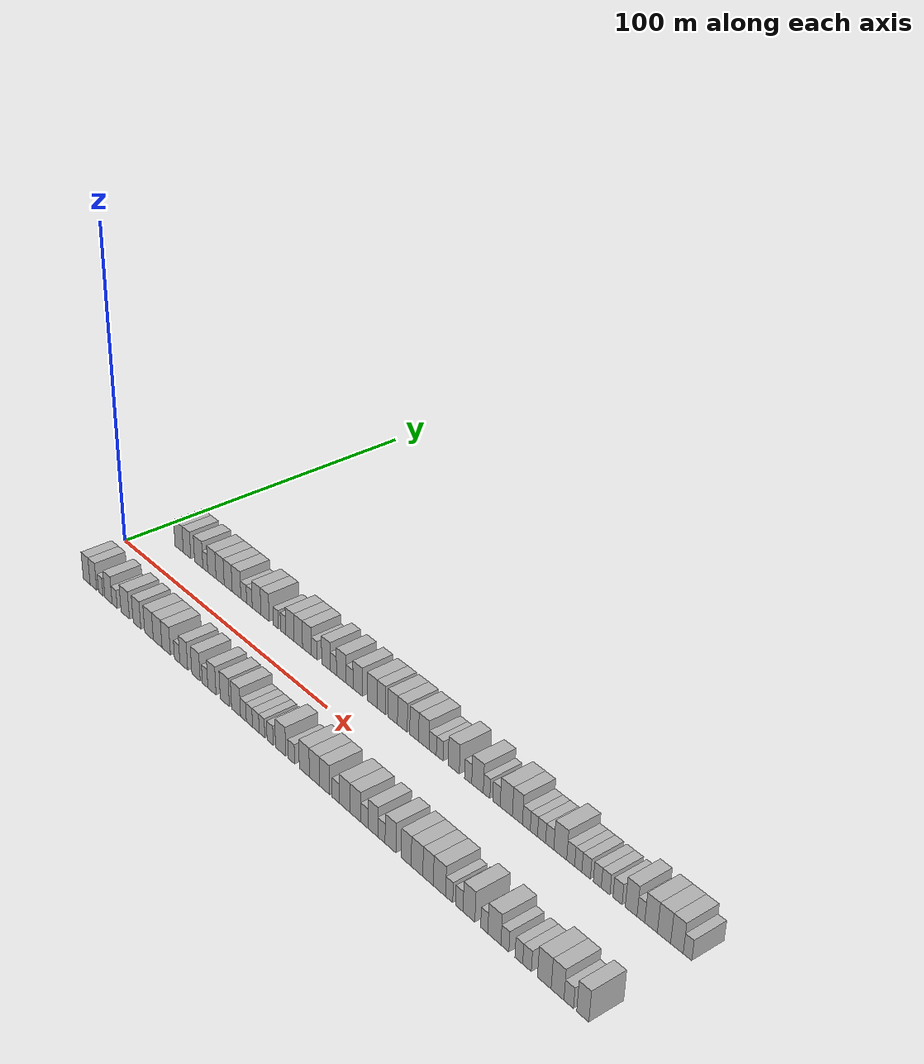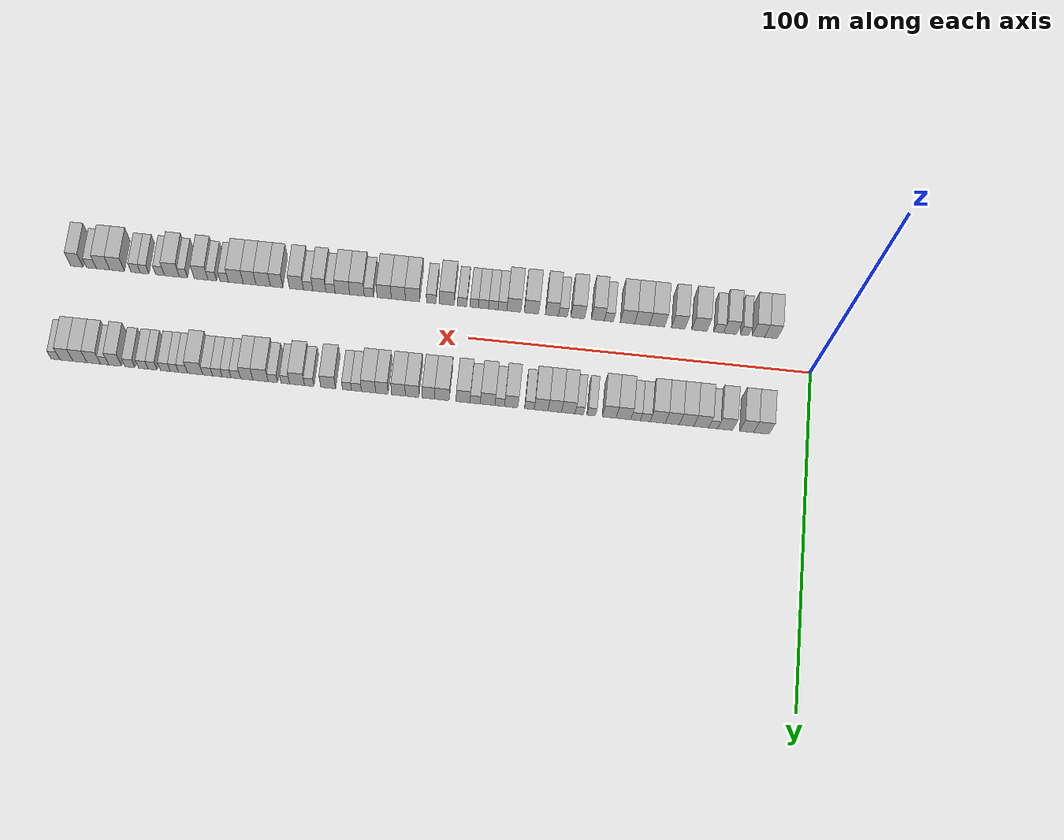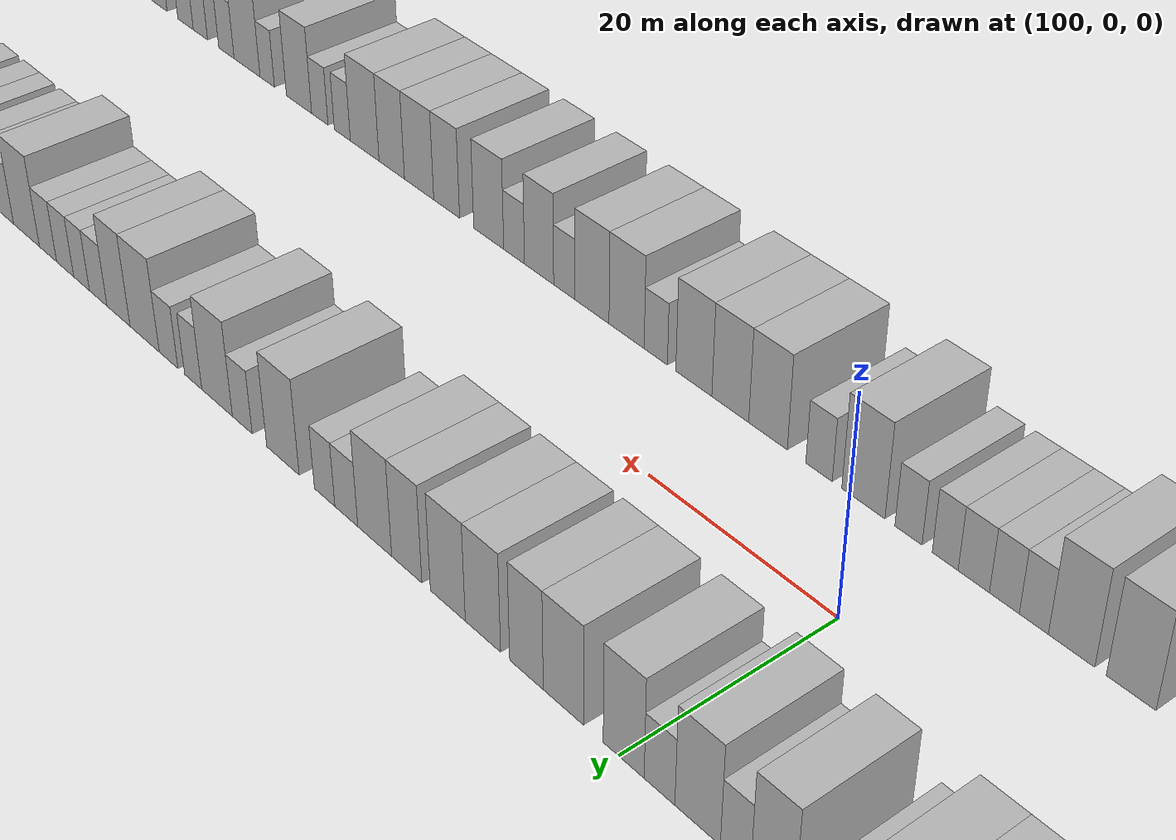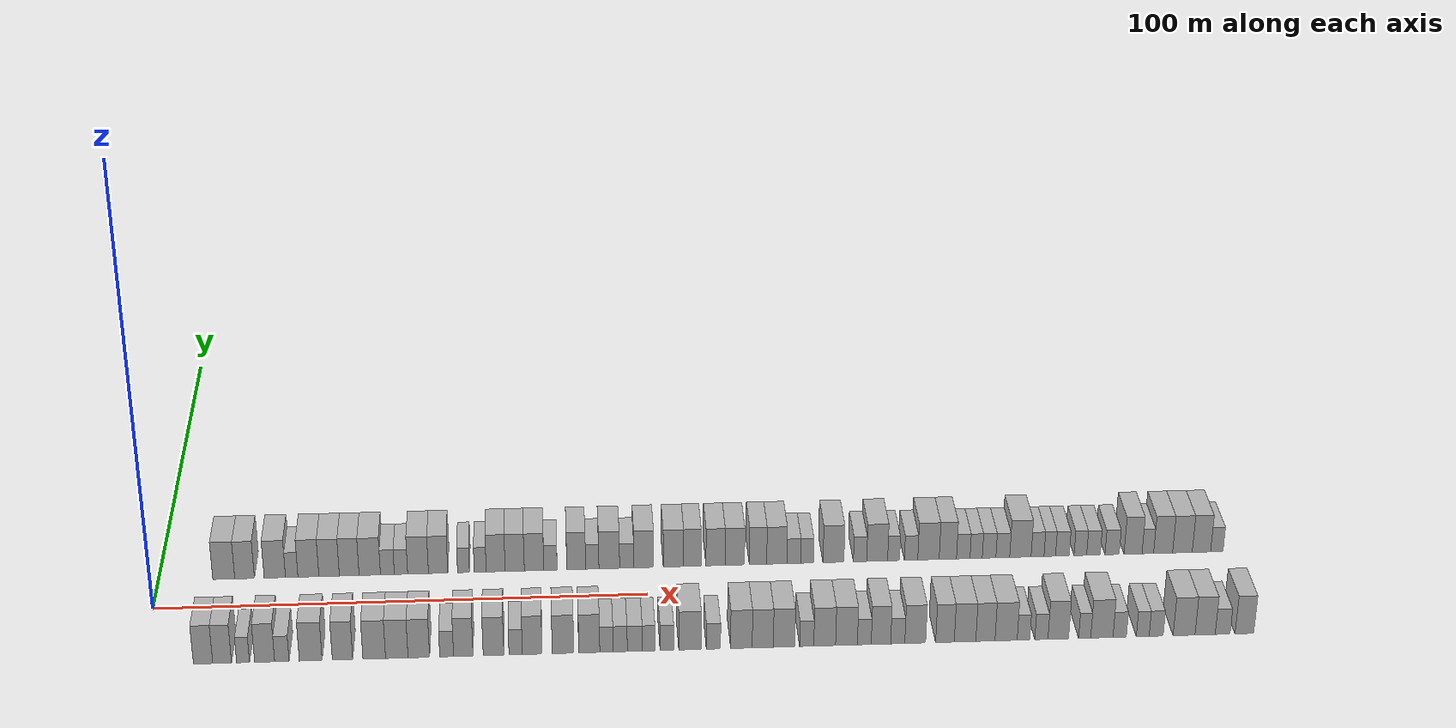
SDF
<sdf version="1.6">
 <world name="default">
  <scene>
   <sky><clouds><speed>12</speed></clouds></sky>
   <ambient>0.4 0.4 0.4 1</ambient>
   <background>0.7 0.7 0.7 1</background>
   <shadows>1</shadows>
  </scene>
  <gravity>0 0 -9.8066</gravity>
  <magnetic_field>6e-06 2.3e-05 -4.2e-05</magnetic_field>
  <physics default="0" name="default_physics" type="ode">
   <ode>
    <solver>
     <type>quick</type>
     <iters>10</iters>
     <sor>1.0</sor>
     <use_dynamic_moi_rescaling>0</use_dynamic_moi_rescaling>
    </solver>
    <constraints>
     <cfm>0</cfm>
     <erp>0.2</erp>
     <contact_max_correcting_vel>100</contact_max_correcting_vel>
     <contact_surface_layer>0.001</contact_surface_layer>
    </constraints>
   </ode>
   <max_step_size>0.004</max_step_size>
   <real_time_factor>1</real_time_factor>
   <real_time_update_rate>250</real_time_update_rate>
  </physics>
  <light name="sun" type="directional">
   <pose>0 0 10 0 0 0</pose>
   <diffuse>0.8 0.8 0.8 1</diffuse>
   <specular>0.2 0.2 0.2 1</specular>
   <attenuation>
    <range>1000</range>
    <constant>0.9</constant>
    <linear>0.01</linear>
    <quadratic>0.001</quadratic>
   </attenuation>
   <direction>-0.5 0.1 -0.9</direction>
  </light>
  <model name="building_1">
   <static>1</static>
   <pose>13.2403 15.0000 0 0.000000 0.000000 1.570796</pose>
   <link name="link">
    <pose>0 0 4.50 0 0 0</pose>
    <collision name="collision"><geometry><box><size>10.0000 4.4805 9.0000</size></box></geometry></collision>
    <visual name="visual">
     <cast_shadows>0</cast_shadows>
     <geometry><box><size>10.0000 4.4805 9.0000</size></box></geometry>
     <material>
      <script>
       <uri>model://HANNAS_wall/materials/scripts</uri>
       <uri>model://HANNAS_wall/materials/textures</uri>
       <name>vrc/HANNAS_wall</name>
      </script>
     </material>
    </visual>
   </link>
  </model>
  <model name="building_2">
   <static>1</static>
   <pose>17.4862 15.0000 0 0.000000 0.000000 1.570796</pose>
   <link name="link">
    <pose>0 0 4.50 0 0 0</pose>
    <collision name="collision"><geometry><box><size>10.0000 4.0113 9.0000</size></box></geometry></collision>
    <visual name="visual">
     <cast_shadows>0</cast_shadows>
     <geometry><box><size>10.0000 4.0113 9.0000</size></box></geometry>
     <material>
      <script>
       <uri>model://HANNAS_wall/materials/scripts</uri>
       <uri>model://HANNAS_wall/materials/textures</uri>
       <name>vrc/HANNAS_wall</name>
      </script>
     </material>
    </visual>
   </link>
  </model>
  <model name="building_3">
   <static>1</static>
   <pose>23.6738 15.0000 0 0.000000 0.000000 1.570796</pose>
   <link name="link">
    <pose>0 0 4.50 0 0 0</pose>
    <collision name="collision"><geometry><box><size>10.0000 4.3640 9.0000</size></box></geometry></collision>
    <visual name="visual">
     <cast_shadows>0</cast_shadows>
     <geometry><box><size>10.0000 4.3640 9.0000</size></box></geometry>
     <material>
      <script>
       <uri>model://HANNAS_wall/materials/scripts</uri>
       <uri>model://HANNAS_wall/materials/textures</uri>
       <name>vrc/HANNAS_wall</name>
      </script>
     </material>
    </visual>
   </link>
  </model>
  <model name="building_4">
   <static>1</static>
   <pose>27.1243 15.0000 0 0.000000 0.000000 1.570796</pose>
   <link name="link">
    <pose>0 0 3.00 0 0 0</pose>
    <collision name="collision"><geometry><box><size>10.0000 2.5370 6.0000</size></box></geometry></collision>
    <visual name="visual">
     <cast_shadows>0</cast_shadows>
     <geometry><box><size>10.0000 2.5370 6.0000</size></box></geometry>
     <material>
      <script>
       <uri>model://HANNAS_wall/materials/scripts</uri>
       <uri>model://HANNAS_wall/materials/textures</uri>
       <name>vrc/HANNAS_wall</name>
      </script>
     </material>
    </visual>
   </link>
  </model>
  <model name="building_5">
   <static>1</static>
   <pose>30.5359 15.0000 0 0.000000 0.000000 1.570796</pose>
   <link name="link">
    <pose>0 0 4.50 0 0 0</pose>
    <collision name="collision"><geometry><box><size>10.0000 4.2863 9.0000</size></box></geometry></collision>
    <visual name="visual">
     <cast_shadows>0</cast_shadows>
     <geometry><box><size>10.0000 4.2863 9.0000</size></box></geometry>
     <material>
      <script>
       <uri>model://HANNAS_wall/materials/scripts</uri>
       <uri>model://HANNAS_wall/materials/textures</uri>
       <name>vrc/HANNAS_wall</name>
      </script>
     </material>
    </visual>
   </link>
  </model>
  <model name="building_6">
   <static>1</static>
   <pose>34.7743 15.0000 0 0.000000 0.000000 1.570796</pose>
   <link name="link">
    <pose>0 0 4.50 0 0 0</pose>
    <collision name="collision"><geometry><box><size>10.0000 4.1904 9.0000</size></box></geometry></collision>
    <visual name="visual">
     <cast_shadows>0</cast_shadows>
     <geometry><box><size>10.0000 4.1904 9.0000</size></box></geometry>
     <material>
      <script>
       <uri>model://HANNAS_wall/materials/scripts</uri>
       <uri>model://HANNAS_wall/materials/textures</uri>
       <name>vrc/HANNAS_wall</name>
      </script>
     </material>
    </visual>
   </link>
  </model>
  <model name="building_7">
   <static>1</static>
   <pose>38.8950 15.0000 0 0.000000 0.000000 1.570796</pose>
   <link name="link">
    <pose>0 0 4.50 0 0 0</pose>
    <collision name="collision"><geometry><box><size>10.0000 4.0511 9.0000</size></box></geometry></collision>
    <visual name="visual">
     <cast_shadows>0</cast_shadows>
     <geometry><box><size>10.0000 4.0511 9.0000</size></box></geometry>
     <material>
      <script>
       <uri>model://HANNAS_wall/materials/scripts</uri>
       <uri>model://HANNAS_wall/materials/textures</uri>
       <name>vrc/HANNAS_wall</name>
      </script>
     </material>
    </visual>
   </link>
  </model>
  <model name="building_8">
   <static>1</static>
   <pose>43.1086 15.0000 0 0.000000 0.000000 1.570796</pose>
   <link name="link">
    <pose>0 0 4.50 0 0 0</pose>
    <collision name="collision"><geometry><box><size>10.0000 4.3761 9.0000</size></box></geometry></collision>
    <visual name="visual">
     <cast_shadows>0</cast_shadows>
     <geometry><box><size>10.0000 4.3761 9.0000</size></box></geometry>
     <material>
      <script>
       <uri>model://HANNAS_wall/materials/scripts</uri>
       <uri>model://HANNAS_wall/materials/textures</uri>
       <name>vrc/HANNAS_wall</name>
      </script>
     </material>
    </visual>
   </link>
  </model>
  <model name="building_9">
   <static>1</static>
   <pose>46.7246 15.0000 0 0.000000 0.000000 1.570796</pose>
   <link name="link">
    <pose>0 0 3.00 0 0 0</pose>
    <collision name="collision"><geometry><box><size>10.0000 2.8559 6.0000</size></box></geometry></collision>
    <visual name="visual">
     <cast_shadows>0</cast_shadows>
     <geometry><box><size>10.0000 2.8559 6.0000</size></box></geometry>
     <material>
      <script>
       <uri>model://HANNAS_wall/materials/scripts</uri>
       <uri>model://HANNAS_wall/materials/textures</uri>
       <name>vrc/HANNAS_wall</name>
      </script>
     </material>
    </visual>
   </link>
  </model>
  <model name="building_10">
   <static>1</static>
   <pose>49.5225 15.0000 0 0.000000 0.000000 1.570796</pose>
   <link name="link">
    <pose>0 0 3.00 0 0 0</pose>
    <collision name="collision"><geometry><box><size>10.0000 2.7400 6.0000</size></box></geometry></collision>
    <visual name="visual">
     <cast_shadows>0</cast_shadows>
     <geometry><box><size>10.0000 2.7400 6.0000</size></box></geometry>
     <material>
      <script>
       <uri>model://HANNAS_wall/materials/scripts</uri>
       <uri>model://HANNAS_wall/materials/textures</uri>
       <name>vrc/HANNAS_wall</name>
      </script>
     </material>
    </visual>
   </link>
  </model>
  <model name="building_11">
   <static>1</static>
   <pose>53.0292 15.0000 0 0.000000 0.000000 1.570796</pose>
   <link name="link">
    <pose>0 0 4.50 0 0 0</pose>
    <collision name="collision"><geometry><box><size>10.0000 4.2733 9.0000</size></box></geometry></collision>
    <visual name="visual">
     <cast_shadows>0</cast_shadows>
     <geometry><box><size>10.0000 4.2733 9.0000</size></box></geometry>
     <material>
      <script>
       <uri>model://HANNAS_wall/materials/scripts</uri>
       <uri>model://HANNAS_wall/materials/textures</uri>
       <name>vrc/HANNAS_wall</name>
      </script>
     </material>
    </visual>
   </link>
  </model>
  <model name="building_12">
   <static>1</static>
   <pose>57.1540 15.0000 0 0.000000 0.000000 1.570796</pose>
   <link name="link">
    <pose>0 0 4.50 0 0 0</pose>
    <collision name="collision"><geometry><box><size>10.0000 3.9763 9.0000</size></box></geometry></collision>
    <visual name="visual">
     <cast_shadows>0</cast_shadows>
     <geometry><box><size>10.0000 3.9763 9.0000</size></box></geometry>
     <material>
      <script>
       <uri>model://HANNAS_wall/materials/scripts</uri>
       <uri>model://HANNAS_wall/materials/textures</uri>
       <name>vrc/HANNAS_wall</name>
      </script>
     </material>
    </visual>
   </link>
  </model>
  <model name="building_13">
   <static>1</static>
   <pose>62.3634 15.0000 0 0.000000 0.000000 1.570796</pose>
   <link name="link">
    <pose>0 0 3.00 0 0 0</pose>
    <collision name="collision"><geometry><box><size>10.0000 2.4425 6.0000</size></box></geometry></collision>
    <visual name="visual">
     <cast_shadows>0</cast_shadows>
     <geometry><box><size>10.0000 2.4425 6.0000</size></box></geometry>
     <material>
      <script>
       <uri>model://HANNAS_wall/materials/scripts</uri>
       <uri>model://HANNAS_wall/materials/textures</uri>
       <name>vrc/HANNAS_wall</name>
      </script>
     </material>
    </visual>
   </link>
  </model>
  <model name="building_14">
   <static>1</static>
   <pose>65.8140 15.0000 0 0.000000 0.000000 1.570796</pose>
   <link name="link">
    <pose>0 0 3.00 0 0 0</pose>
    <collision name="collision"><geometry><box><size>10.0000 2.4586 6.0000</size></box></geometry></collision>
    <visual name="visual">
     <cast_shadows>0</cast_shadows>
     <geometry><box><size>10.0000 2.4586 6.0000</size></box></geometry>
     <material>
      <script>
       <uri>model://HANNAS_wall/materials/scripts</uri>
       <uri>model://HANNAS_wall/materials/textures</uri>
       <name>vrc/HANNAS_wall</name>
      </script>
     </material>
    </visual>
   </link>
  </model>
  <model name="building_15">
   <static>1</static>
   <pose>68.9917 15.0000 0 0.000000 0.000000 1.570796</pose>
   <link name="link">
    <pose>0 0 4.50 0 0 0</pose>
    <collision name="collision"><geometry><box><size>10.0000 3.8968 9.0000</size></box></geometry></collision>
    <visual name="visual">
     <cast_shadows>0</cast_shadows>
     <geometry><box><size>10.0000 3.8968 9.0000</size></box></geometry>
     <material>
      <script>
       <uri>model://HANNAS_wall/materials/scripts</uri>
       <uri>model://HANNAS_wall/materials/textures</uri>
       <name>vrc/HANNAS_wall</name>
      </script>
     </material>
    </visual>
   </link>
  </model>
  <model name="building_16">
   <static>1</static>
   <pose>72.9153 15.0000 0 0.000000 0.000000 1.570796</pose>
   <link name="link">
    <pose>0 0 4.50 0 0 0</pose>
    <collision name="collision"><geometry><box><size>10.0000 3.9504 9.0000</size></box></geometry></collision>
    <visual name="visual">
     <cast_shadows>0</cast_shadows>
     <geometry><box><size>10.0000 3.9504 9.0000</size></box></geometry>
     <material>
      <script>
       <uri>model://HANNAS_wall/materials/scripts</uri>
       <uri>model://HANNAS_wall/materials/textures</uri>
       <name>vrc/HANNAS_wall</name>
      </script>
     </material>
    </visual>
   </link>
  </model>
  <model name="building_17">
   <static>1</static>
   <pose>76.8977 15.0000 0 0.000000 0.000000 1.570796</pose>
   <link name="link">
    <pose>0 0 4.50 0 0 0</pose>
    <collision name="collision"><geometry><box><size>10.0000 4.0143 9.0000</size></box></geometry></collision>
    <visual name="visual">
     <cast_shadows>0</cast_shadows>
     <geometry><box><size>10.0000 4.0143 9.0000</size></box></geometry>
     <material>
      <script>
       <uri>model://HANNAS_wall/materials/scripts</uri>
       <uri>model://HANNAS_wall/materials/textures</uri>
       <name>vrc/HANNAS_wall</name>
      </script>
     </material>
    </visual>
   </link>
  </model>
  <model name="building_18">
   <static>1</static>
   <pose>80.2734 15.0000 0 0.000000 0.000000 1.570796</pose>
   <link name="link">
    <pose>0 0 3.00 0 0 0</pose>
    <collision name="collision"><geometry><box><size>10.0000 2.7371 6.0000</size></box></geometry></collision>
    <visual name="visual">
     <cast_shadows>0</cast_shadows>
     <geometry><box><size>10.0000 2.7371 6.0000</size></box></geometry>
     <material>
      <script>
       <uri>model://HANNAS_wall/materials/scripts</uri>
       <uri>model://HANNAS_wall/materials/textures</uri>
       <name>vrc/HANNAS_wall</name>
      </script>
     </material>
    </visual>
   </link>
  </model>
  <model name="building_19">
   <static>1</static>
   <pose>85.5805 15.0000 0 0.000000 0.000000 1.570796</pose>
   <link name="link">
    <pose>0 0 4.50 0 0 0</pose>
    <collision name="collision"><geometry><box><size>10.0000 3.8772 9.0000</size></box></geometry></collision>
    <visual name="visual">
     <cast_shadows>0</cast_shadows>
     <geometry><box><size>10.0000 3.8772 9.0000</size></box></geometry>
     <material>
      <script>
       <uri>model://HANNAS_wall/materials/scripts</uri>
       <uri>model://HANNAS_wall/materials/textures</uri>
       <name>vrc/HANNAS_wall</name>
      </script>
     </material>
    </visual>
   </link>
  </model>
  <model name="building_20">
   <static>1</static>
   <pose>88.8902 15.0000 0 0.000000 0.000000 1.570796</pose>
   <link name="link">
    <pose>0 0 3.00 0 0 0</pose>
    <collision name="collision"><geometry><box><size>10.0000 2.7421 6.0000</size></box></geometry></collision>
    <visual name="visual">
     <cast_shadows>0</cast_shadows>
     <geometry><box><size>10.0000 2.7421 6.0000</size></box></geometry>
     <material>
      <script>
       <uri>model://HANNAS_wall/materials/scripts</uri>
       <uri>model://HANNAS_wall/materials/textures</uri>
       <name>vrc/HANNAS_wall</name>
      </script>
     </material>
    </visual>
   </link>
  </model>
  <model name="building_21">
   <static>1</static>
   <pose>92.3960 15.0000 0 0.000000 0.000000 1.570796</pose>
   <link name="link">
    <pose>0 0 4.50 0 0 0</pose>
    <collision name="collision"><geometry><box><size>10.0000 4.2694 9.0000</size></box></geometry></collision>
    <visual name="visual">
     <cast_shadows>0</cast_shadows>
     <geometry><box><size>10.0000 4.2694 9.0000</size></box></geometry>
     <material>
      <script>
       <uri>model://HANNAS_wall/materials/scripts</uri>
       <uri>model://HANNAS_wall/materials/textures</uri>
       <name>vrc/HANNAS_wall</name>
      </script>
     </material>
    </visual>
   </link>
  </model>
  <model name="building_22">
   <static>1</static>
   <pose>96.0144 15.0000 0 0.000000 0.000000 1.570796</pose>
   <link name="link">
    <pose>0 0 3.00 0 0 0</pose>
    <collision name="collision"><geometry><box><size>10.0000 2.9675 6.0000</size></box></geometry></collision>
    <visual name="visual">
     <cast_shadows>0</cast_shadows>
     <geometry><box><size>10.0000 2.9675 6.0000</size></box></geometry>
     <material>
      <script>
       <uri>model://HANNAS_wall/materials/scripts</uri>
       <uri>model://HANNAS_wall/materials/textures</uri>
       <name>vrc/HANNAS_wall</name>
      </script>
     </material>
    </visual>
   </link>
  </model>
  <model name="building_23">
   <static>1</static>
   <pose>99.5372 15.0000 0 0.000000 0.000000 1.570796</pose>
   <link name="link">
    <pose>0 0 4.50 0 0 0</pose>
    <collision name="collision"><geometry><box><size>10.0000 4.0781 9.0000</size></box></geometry></collision>
    <visual name="visual">
     <cast_shadows>0</cast_shadows>
     <geometry><box><size>10.0000 4.0781 9.0000</size></box></geometry>
     <material>
      <script>
       <uri>model://HANNAS_wall/materials/scripts</uri>
       <uri>model://HANNAS_wall/materials/textures</uri>
       <name>vrc/HANNAS_wall</name>
      </script>
     </material>
    </visual>
   </link>
  </model>
  <model name="building_24">
   <static>1</static>
   <pose>105.6839 15.0000 0 0.000000 0.000000 1.570796</pose>
   <link name="link">
    <pose>0 0 4.50 0 0 0</pose>
    <collision name="collision"><geometry><box><size>10.0000 4.2154 9.0000</size></box></geometry></collision>
    <visual name="visual">
     <cast_shadows>0</cast_shadows>
     <geometry><box><size>10.0000 4.2154 9.0000</size></box></geometry>
     <material>
      <script>
       <uri>model://HANNAS_wall/materials/scripts</uri>
       <uri>model://HANNAS_wall/materials/textures</uri>
       <name>vrc/HANNAS_wall</name>
      </script>
     </material>
    </visual>
   </link>
  </model>
  <model name="building_25">
   <static>1</static>
   <pose>109.6026 15.0000 0 0.000000 0.000000 1.570796</pose>
   <link name="link">
    <pose>0 0 4.50 0 0 0</pose>
    <collision name="collision"><geometry><box><size>10.0000 3.6221 9.0000</size></box></geometry></collision>
    <visual name="visual">
     <cast_shadows>0</cast_shadows>
     <geometry><box><size>10.0000 3.6221 9.0000</size></box></geometry>
     <material>
      <script>
       <uri>model://HANNAS_wall/materials/scripts</uri>
       <uri>model://HANNAS_wall/materials/textures</uri>
       <name>vrc/HANNAS_wall</name>
      </script>
     </material>
    </visual>
   </link>
  </model>
  <model name="building_26">
   <static>1</static>
   <pose>114.3878 15.0000 0 0.000000 0.000000 1.570796</pose>
   <link name="link">
    <pose>0 0 4.50 0 0 0</pose>
    <collision name="collision"><geometry><box><size>10.0000 3.9483 9.0000</size></box></geometry></collision>
    <visual name="visual">
     <cast_shadows>0</cast_shadows>
     <geometry><box><size>10.0000 3.9483 9.0000</size></box></geometry>
     <material>
      <script>
       <uri>model://HANNAS_wall/materials/scripts</uri>
       <uri>model://HANNAS_wall/materials/textures</uri>
       <name>vrc/HANNAS_wall</name>
      </script>
     </material>
    </visual>
   </link>
  </model>
  <model name="building_27">
   <static>1</static>
   <pose>118.3760 15.0000 0 0.000000 0.000000 1.570796</pose>
   <link name="link">
    <pose>0 0 4.50 0 0 0</pose>
    <collision name="collision"><geometry><box><size>10.0000 4.0280 9.0000</size></box></geometry></collision>
    <visual name="visual">
     <cast_shadows>0</cast_shadows>
     <geometry><box><size>10.0000 4.0280 9.0000</size></box></geometry>
     <material>
      <script>
       <uri>model://HANNAS_wall/materials/scripts</uri>
       <uri>model://HANNAS_wall/materials/textures</uri>
       <name>vrc/HANNAS_wall</name>
      </script>
     </material>
    </visual>
   </link>
  </model>
  <model name="building_28">
   <static>1</static>
   <pose>123.1927 15.0000 0 0.000000 0.000000 1.570796</pose>
   <link name="link">
    <pose>0 0 4.50 0 0 0</pose>
    <collision name="collision"><geometry><box><size>10.0000 3.6054 9.0000</size></box></geometry></collision>
    <visual name="visual">
     <cast_shadows>0</cast_shadows>
     <geometry><box><size>10.0000 3.6054 9.0000</size></box></geometry>
     <material>
      <script>
       <uri>model://HANNAS_wall/materials/scripts</uri>
       <uri>model://HANNAS_wall/materials/textures</uri>
       <name>vrc/HANNAS_wall</name>
      </script>
     </material>
    </visual>
   </link>
  </model>
  <model name="building_29">
   <static>1</static>
   <pose>127.0830 15.0000 0 0.000000 0.000000 1.570796</pose>
   <link name="link">
    <pose>0 0 4.50 0 0 0</pose>
    <collision name="collision"><geometry><box><size>10.0000 4.1753 9.0000</size></box></geometry></collision>
    <visual name="visual">
     <cast_shadows>0</cast_shadows>
     <geometry><box><size>10.0000 4.1753 9.0000</size></box></geometry>
     <material>
      <script>
       <uri>model://HANNAS_wall/materials/scripts</uri>
       <uri>model://HANNAS_wall/materials/textures</uri>
       <name>vrc/HANNAS_wall</name>
      </script>
     </material>
    </visual>
   </link>
  </model>
  <model name="building_30">
   <static>1</static>
   <pose>130.6172 15.0000 0 0.000000 0.000000 1.570796</pose>
   <link name="link">
    <pose>0 0 3.00 0 0 0</pose>
    <collision name="collision"><geometry><box><size>10.0000 2.8932 6.0000</size></box></geometry></collision>
    <visual name="visual">
     <cast_shadows>0</cast_shadows>
     <geometry><box><size>10.0000 2.8932 6.0000</size></box></geometry>
     <material>
      <script>
       <uri>model://HANNAS_wall/materials/scripts</uri>
       <uri>model://HANNAS_wall/materials/textures</uri>
       <name>vrc/HANNAS_wall</name>
      </script>
     </material>
    </visual>
   </link>
  </model>
  <model name="building_31">
   <static>1</static>
   <pose>133.3781 15.0000 0 0.000000 0.000000 1.570796</pose>
   <link name="link">
    <pose>0 0 3.00 0 0 0</pose>
    <collision name="collision"><geometry><box><size>10.0000 2.6285 6.0000</size></box></geometry></collision>
    <visual name="visual">
     <cast_shadows>0</cast_shadows>
     <geometry><box><size>10.0000 2.6285 6.0000</size></box></geometry>
     <material>
      <script>
       <uri>model://HANNAS_wall/materials/scripts</uri>
       <uri>model://HANNAS_wall/materials/textures</uri>
       <name>vrc/HANNAS_wall</name>
      </script>
     </material>
    </visual>
   </link>
  </model>
  <model name="building_32">
   <static>1</static>
   <pose>138.8617 15.0000 0 0.000000 0.000000 1.570796</pose>
   <link name="link">
    <pose>0 0 4.50 0 0 0</pose>
    <collision name="collision"><geometry><box><size>10.0000 4.3386 9.0000</size></box></geometry></collision>
    <visual name="visual">
     <cast_shadows>0</cast_shadows>
     <geometry><box><size>10.0000 4.3386 9.0000</size></box></geometry>
     <material>
      <script>
       <uri>model://HANNAS_wall/materials/scripts</uri>
       <uri>model://HANNAS_wall/materials/textures</uri>
       <name>vrc/HANNAS_wall</name>
      </script>
     </material>
    </visual>
   </link>
  </model>
  <model name="building_33">
   <static>1</static>
   <pose>144.4029 15.0000 0 0.000000 0.000000 1.570796</pose>
   <link name="link">
    <pose>0 0 3.00 0 0 0</pose>
    <collision name="collision"><geometry><box><size>10.0000 2.7437 6.0000</size></box></geometry></collision>
    <visual name="visual">
     <cast_shadows>0</cast_shadows>
     <geometry><box><size>10.0000 2.7437 6.0000</size></box></geometry>
     <material>
      <script>
       <uri>model://HANNAS_wall/materials/scripts</uri>
       <uri>model://HANNAS_wall/materials/textures</uri>
       <name>vrc/HANNAS_wall</name>
      </script>
     </material>
    </visual>
   </link>
  </model>
  <model name="building_34">
   <static>1</static>
   <pose>147.9562 15.0000 0 0.000000 0.000000 1.570796</pose>
   <link name="link">
    <pose>0 0 4.50 0 0 0</pose>
    <collision name="collision"><geometry><box><size>10.0000 4.3629 9.0000</size></box></geometry></collision>
    <visual name="visual">
     <cast_shadows>0</cast_shadows>
     <geometry><box><size>10.0000 4.3629 9.0000</size></box></geometry>
     <material>
      <script>
       <uri>model://HANNAS_wall/materials/scripts</uri>
       <uri>model://HANNAS_wall/materials/textures</uri>
       <name>vrc/HANNAS_wall</name>
      </script>
     </material>
    </visual>
   </link>
  </model>
  <model name="building_35">
   <static>1</static>
   <pose>151.3836 15.0000 0 0.000000 0.000000 1.570796</pose>
   <link name="link">
    <pose>0 0 3.00 0 0 0</pose>
    <collision name="collision"><geometry><box><size>10.0000 2.4920 6.0000</size></box></geometry></collision>
    <visual name="visual">
     <cast_shadows>0</cast_shadows>
     <geometry><box><size>10.0000 2.4920 6.0000</size></box></geometry>
     <material>
      <script>
       <uri>model://HANNAS_wall/materials/scripts</uri>
       <uri>model://HANNAS_wall/materials/textures</uri>
       <name>vrc/HANNAS_wall</name>
      </script>
     </material>
    </visual>
   </link>
  </model>
  <model name="building_36">
   <static>1</static>
   <pose>155.0240 15.0000 0 0.000000 0.000000 1.570796</pose>
   <link name="link">
    <pose>0 0 3.00 0 0 0</pose>
    <collision name="collision"><geometry><box><size>10.0000 2.7888 6.0000</size></box></geometry></collision>
    <visual name="visual">
     <cast_shadows>0</cast_shadows>
     <geometry><box><size>10.0000 2.7888 6.0000</size></box></geometry>
     <material>
      <script>
       <uri>model://HANNAS_wall/materials/scripts</uri>
       <uri>model://HANNAS_wall/materials/textures</uri>
       <name>vrc/HANNAS_wall</name>
      </script>
     </material>
    </visual>
   </link>
  </model>
  <model name="building_37">
   <static>1</static>
   <pose>158.6517 15.0000 0 0.000000 0.000000 1.570796</pose>
   <link name="link">
    <pose>0 0 4.50 0 0 0</pose>
    <collision name="collision"><geometry><box><size>10.0000 4.4665 9.0000</size></box></geometry></collision>
    <visual name="visual">
     <cast_shadows>0</cast_shadows>
     <geometry><box><size>10.0000 4.4665 9.0000</size></box></geometry>
     <material>
      <script>
       <uri>model://HANNAS_wall/materials/scripts</uri>
       <uri>model://HANNAS_wall/materials/textures</uri>
       <name>vrc/HANNAS_wall</name>
      </script>
     </material>
    </visual>
   </link>
  </model>
  <model name="building_38">
   <static>1</static>
   <pose>162.6968 15.0000 0 0.000000 0.000000 1.570796</pose>
   <link name="link">
    <pose>0 0 4.50 0 0 0</pose>
    <collision name="collision"><geometry><box><size>10.0000 3.6238 9.0000</size></box></geometry></collision>
    <visual name="visual">
     <cast_shadows>0</cast_shadows>
     <geometry><box><size>10.0000 3.6238 9.0000</size></box></geometry>
     <material>
      <script>
       <uri>model://HANNAS_wall/materials/scripts</uri>
       <uri>model://HANNAS_wall/materials/textures</uri>
       <name>vrc/HANNAS_wall</name>
      </script>
     </material>
    </visual>
   </link>
  </model>
  <model name="building_39">
   <static>1</static>
   <pose>165.9192 15.0000 0 0.000000 0.000000 1.570796</pose>
   <link name="link">
    <pose>0 0 3.00 0 0 0</pose>
    <collision name="collision"><geometry><box><size>10.0000 2.8211 6.0000</size></box></geometry></collision>
    <visual name="visual">
     <cast_shadows>0</cast_shadows>
     <geometry><box><size>10.0000 2.8211 6.0000</size></box></geometry>
     <material>
      <script>
       <uri>model://HANNAS_wall/materials/scripts</uri>
       <uri>model://HANNAS_wall/materials/textures</uri>
       <name>vrc/HANNAS_wall</name>
      </script>
     </material>
    </visual>
   </link>
  </model>
  <model name="building_40">
   <static>1</static>
   <pose>168.6110 15.0000 0 0.000000 0.000000 1.570796</pose>
   <link name="link">
    <pose>0 0 3.00 0 0 0</pose>
    <collision name="collision"><geometry><box><size>10.0000 2.5624 6.0000</size></box></geometry></collision>
    <visual name="visual">
     <cast_shadows>0</cast_shadows>
     <geometry><box><size>10.0000 2.5624 6.0000</size></box></geometry>
     <material>
      <script>
       <uri>model://HANNAS_wall/materials/scripts</uri>
       <uri>model://HANNAS_wall/materials/textures</uri>
       <name>vrc/HANNAS_wall</name>
      </script>
     </material>
    </visual>
   </link>
  </model>
  <model name="building_41">
   <static>1</static>
   <pose>171.3134 15.0000 0 0.000000 0.000000 1.570796</pose>
   <link name="link">
    <pose>0 0 3.00 0 0 0</pose>
    <collision name="collision"><geometry><box><size>10.0000 2.8425 6.0000</size></box></geometry></collision>
    <visual name="visual">
     <cast_shadows>0</cast_shadows>
     <geometry><box><size>10.0000 2.8425 6.0000</size></box></geometry>
     <material>
      <script>
       <uri>model://HANNAS_wall/materials/scripts</uri>
       <uri>model://HANNAS_wall/materials/textures</uri>
       <name>vrc/HANNAS_wall</name>
      </script>
     </material>
    </visual>
   </link>
  </model>
  <model name="building_42">
   <static>1</static>
   <pose>174.1806 15.0000 0 0.000000 0.000000 1.570796</pose>
   <link name="link">
    <pose>0 0 3.00 0 0 0</pose>
    <collision name="collision"><geometry><box><size>10.0000 2.8918 6.0000</size></box></geometry></collision>
    <visual name="visual">
     <cast_shadows>0</cast_shadows>
     <geometry><box><size>10.0000 2.8918 6.0000</size></box></geometry>
     <material>
      <script>
       <uri>model://HANNAS_wall/materials/scripts</uri>
       <uri>model://HANNAS_wall/materials/textures</uri>
       <name>vrc/HANNAS_wall</name>
      </script>
     </material>
    </visual>
   </link>
  </model>
  <model name="building_43">
   <static>1</static>
   <pose>177.8587 15.0000 0 0.000000 0.000000 1.570796</pose>
   <link name="link">
    <pose>0 0 4.50 0 0 0</pose>
    <collision name="collision"><geometry><box><size>10.0000 4.4644 9.0000</size></box></geometry></collision>
    <visual name="visual">
     <cast_shadows>0</cast_shadows>
     <geometry><box><size>10.0000 4.4644 9.0000</size></box></geometry>
     <material>
      <script>
       <uri>model://HANNAS_wall/materials/scripts</uri>
       <uri>model://HANNAS_wall/materials/textures</uri>
       <name>vrc/HANNAS_wall</name>
      </script>
     </material>
    </visual>
   </link>
  </model>
  <model name="building_44">
   <static>1</static>
   <pose>181.4485 15.0000 0 0.000000 0.000000 1.570796</pose>
   <link name="link">
    <pose>0 0 3.00 0 0 0</pose>
    <collision name="collision"><geometry><box><size>10.0000 2.7152 6.0000</size></box></geometry></collision>
    <visual name="visual">
     <cast_shadows>0</cast_shadows>
     <geometry><box><size>10.0000 2.7152 6.0000</size></box></geometry>
     <material>
      <script>
       <uri>model://HANNAS_wall/materials/scripts</uri>
       <uri>model://HANNAS_wall/materials/textures</uri>
       <name>vrc/HANNAS_wall</name>
      </script>
     </material>
    </visual>
   </link>
  </model>
  <model name="building_45">
   <static>1</static>
   <pose>184.0129 15.0000 0 0.000000 0.000000 1.570796</pose>
   <link name="link">
    <pose>0 0 3.00 0 0 0</pose>
    <collision name="collision"><geometry><box><size>10.0000 2.4135 6.0000</size></box></geometry></collision>
    <visual name="visual">
     <cast_shadows>0</cast_shadows>
     <geometry><box><size>10.0000 2.4135 6.0000</size></box></geometry>
     <material>
      <script>
       <uri>model://HANNAS_wall/materials/scripts</uri>
       <uri>model://HANNAS_wall/materials/textures</uri>
       <name>vrc/HANNAS_wall</name>
      </script>
     </material>
    </visual>
   </link>
  </model>
  <model name="building_46">
   <static>1</static>
   <pose>186.6566 15.0000 0 0.000000 0.000000 1.570796</pose>
   <link name="link">
    <pose>0 0 3.00 0 0 0</pose>
    <collision name="collision"><geometry><box><size>10.0000 2.8739 6.0000</size></box></geometry></collision>
    <visual name="visual">
     <cast_shadows>0</cast_shadows>
     <geometry><box><size>10.0000 2.8739 6.0000</size></box></geometry>
     <material>
      <script>
       <uri>model://HANNAS_wall/materials/scripts</uri>
       <uri>model://HANNAS_wall/materials/textures</uri>
       <name>vrc/HANNAS_wall</name>
      </script>
     </material>
    </visual>
   </link>
  </model>
  <model name="building_47">
   <static>1</static>
   <pose>190.4143 15.0000 0 0.000000 0.000000 1.570796</pose>
   <link name="link">
    <pose>0 0 3.00 0 0 0</pose>
    <collision name="collision"><geometry><box><size>10.0000 2.6414 6.0000</size></box></geometry></collision>
    <visual name="visual">
     <cast_shadows>0</cast_shadows>
     <geometry><box><size>10.0000 2.6414 6.0000</size></box></geometry>
     <material>
      <script>
       <uri>model://HANNAS_wall/materials/scripts</uri>
       <uri>model://HANNAS_wall/materials/textures</uri>
       <name>vrc/HANNAS_wall</name>
      </script>
     </material>
    </visual>
   </link>
  </model>
  <model name="building_48">
   <static>1</static>
   <pose>193.1601 15.0000 0 0.000000 0.000000 1.570796</pose>
   <link name="link">
    <pose>0 0 3.00 0 0 0</pose>
    <collision name="collision"><geometry><box><size>10.0000 2.8502 6.0000</size></box></geometry></collision>
    <visual name="visual">
     <cast_shadows>0</cast_shadows>
     <geometry><box><size>10.0000 2.8502 6.0000</size></box></geometry>
     <material>
      <script>
       <uri>model://HANNAS_wall/materials/scripts</uri>
       <uri>model://HANNAS_wall/materials/textures</uri>
       <name>vrc/HANNAS_wall</name>
      </script>
     </material>
    </visual>
   </link>
  </model>
  <model name="building_49">
   <static>1</static>
   <pose>197.0775 15.0000 0 0.000000 0.000000 1.570796</pose>
   <link name="link">
    <pose>0 0 3.00 0 0 0</pose>
    <collision name="collision"><geometry><box><size>10.0000 2.9847 6.0000</size></box></geometry></collision>
    <visual name="visual">
     <cast_shadows>0</cast_shadows>
     <geometry><box><size>10.0000 2.9847 6.0000</size></box></geometry>
     <material>
      <script>
       <uri>model://HANNAS_wall/materials/scripts</uri>
       <uri>model://HANNAS_wall/materials/textures</uri>
       <name>vrc/HANNAS_wall</name>
      </script>
     </material>
    </visual>
   </link>
  </model>
  <model name="building_50">
   <static>1</static>
   <pose>201.4639 15.0000 0 0.000000 0.000000 1.570796</pose>
   <link name="link">
    <pose>0 0 4.50 0 0 0</pose>
    <collision name="collision"><geometry><box><size>10.0000 3.7880 9.0000</size></box></geometry></collision>
    <visual name="visual">
     <cast_shadows>0</cast_shadows>
     <geometry><box><size>10.0000 3.7880 9.0000</size></box></geometry>
     <material>
      <script>
       <uri>model://HANNAS_wall/materials/scripts</uri>
       <uri>model://HANNAS_wall/materials/textures</uri>
       <name>vrc/HANNAS_wall</name>
      </script>
     </material>
    </visual>
   </link>
  </model>
  <model name="building_51">
   <static>1</static>
   <pose>204.5732 15.0000 0 0.000000 0.000000 1.570796</pose>
   <link name="link">
    <pose>0 0 3.00 0 0 0</pose>
    <collision name="collision"><geometry><box><size>10.0000 2.4307 6.0000</size></box></geometry></collision>
    <visual name="visual">
     <cast_shadows>0</cast_shadows>
     <geometry><box><size>10.0000 2.4307 6.0000</size></box></geometry>
     <material>
      <script>
       <uri>model://HANNAS_wall/materials/scripts</uri>
       <uri>model://HANNAS_wall/materials/textures</uri>
       <name>vrc/HANNAS_wall</name>
      </script>
     </material>
    </visual>
   </link>
  </model>
  <model name="building_52">
   <static>1</static>
   <pose>207.7834 15.0000 0 0.000000 0.000000 1.570796</pose>
   <link name="link">
    <pose>0 0 4.50 0 0 0</pose>
    <collision name="collision"><geometry><box><size>10.0000 3.9896 9.0000</size></box></geometry></collision>
    <visual name="visual">
     <cast_shadows>0</cast_shadows>
     <geometry><box><size>10.0000 3.9896 9.0000</size></box></geometry>
     <material>
      <script>
       <uri>model://HANNAS_wall/materials/scripts</uri>
       <uri>model://HANNAS_wall/materials/textures</uri>
       <name>vrc/HANNAS_wall</name>
      </script>
     </material>
    </visual>
   </link>
  </model>
  <model name="building_53">
   <static>1</static>
   <pose>211.8404 15.0000 0 0.000000 0.000000 1.570796</pose>
   <link name="link">
    <pose>0 0 4.50 0 0 0</pose>
    <collision name="collision"><geometry><box><size>10.0000 4.1246 9.0000</size></box></geometry></collision>
    <visual name="visual">
     <cast_shadows>0</cast_shadows>
     <geometry><box><size>10.0000 4.1246 9.0000</size></box></geometry>
     <material>
      <script>
       <uri>model://HANNAS_wall/materials/scripts</uri>
       <uri>model://HANNAS_wall/materials/textures</uri>
       <name>vrc/HANNAS_wall</name>
      </script>
     </material>
    </visual>
   </link>
  </model>
  <model name="building_54">
   <static>1</static>
   <pose>215.8336 15.0000 0 0.000000 0.000000 1.570796</pose>
   <link name="link">
    <pose>0 0 4.50 0 0 0</pose>
    <collision name="collision"><geometry><box><size>10.0000 3.8618 9.0000</size></box></geometry></collision>
    <visual name="visual">
     <cast_shadows>0</cast_shadows>
     <geometry><box><size>10.0000 3.8618 9.0000</size></box></geometry>
     <material>
      <script>
       <uri>model://HANNAS_wall/materials/scripts</uri>
       <uri>model://HANNAS_wall/materials/textures</uri>
       <name>vrc/HANNAS_wall</name>
      </script>
     </material>
    </visual>
   </link>
  </model>
  <model name="building_55">
   <static>1</static>
   <pose>219.0743 15.0000 0 0.000000 0.000000 1.570796</pose>
   <link name="link">
    <pose>0 0 3.00 0 0 0</pose>
    <collision name="collision"><geometry><box><size>10.0000 2.6194 6.0000</size></box></geometry></collision>
    <visual name="visual">
     <cast_shadows>0</cast_shadows>
     <geometry><box><size>10.0000 2.6194 6.0000</size></box></geometry>
     <material>
      <script>
       <uri>model://HANNAS_wall/materials/scripts</uri>
       <uri>model://HANNAS_wall/materials/textures</uri>
       <name>vrc/HANNAS_wall</name>
      </script>
     </material>
    </visual>
   </link>
  </model>
  <model name="building_56">
   <static>1</static>
   <pose>11.8837 -15.0000 0 0.000000 0.000000 1.570796</pose>
   <link name="link">
    <pose>0 0 4.50 0 0 0</pose>
    <collision name="collision"><geometry><box><size>10.0000 3.7673 9.0000</size></box></geometry></collision>
    <visual name="visual">
     <cast_shadows>0</cast_shadows>
     <geometry><box><size>10.0000 3.7673 9.0000</size></box></geometry>
     <material>
      <script>
       <uri>model://HANNAS_wall/materials/scripts</uri>
       <uri>model://HANNAS_wall/materials/textures</uri>
       <name>vrc/HANNAS_wall</name>
      </script>
     </material>
    </visual>
   </link>
  </model>
  <model name="building_57">
   <static>1</static>
   <pose>15.5975 -15.0000 0 0.000000 0.000000 1.570796</pose>
   <link name="link">
    <pose>0 0 4.50 0 0 0</pose>
    <collision name="collision"><geometry><box><size>10.0000 3.6603 9.0000</size></box></geometry></collision>
    <visual name="visual">
     <cast_shadows>0</cast_shadows>
     <geometry><box><size>10.0000 3.6603 9.0000</size></box></geometry>
     <material>
      <script>
       <uri>model://HANNAS_wall/materials/scripts</uri>
       <uri>model://HANNAS_wall/materials/textures</uri>
       <name>vrc/HANNAS_wall</name>
      </script>
     </material>
    </visual>
   </link>
  </model>
  <model name="building_58">
   <static>1</static>
   <pose>19.6850 -15.0000 0 0.000000 0.000000 1.570796</pose>
   <link name="link">
    <pose>0 0 3.00 0 0 0</pose>
    <collision name="collision"><geometry><box><size>10.0000 2.5149 6.0000</size></box></geometry></collision>
    <visual name="visual">
     <cast_shadows>0</cast_shadows>
     <geometry><box><size>10.0000 2.5149 6.0000</size></box></geometry>
     <material>
      <script>
       <uri>model://HANNAS_wall/materials/scripts</uri>
       <uri>model://HANNAS_wall/materials/textures</uri>
       <name>vrc/HANNAS_wall</name>
      </script>
     </material>
    </visual>
   </link>
  </model>
  <model name="building_59">
   <static>1</static>
   <pose>23.8967 -15.0000 0 0.000000 0.000000 1.570796</pose>
   <link name="link">
    <pose>0 0 4.50 0 0 0</pose>
    <collision name="collision"><geometry><box><size>10.0000 3.9086 9.0000</size></box></geometry></collision>
    <visual name="visual">
     <cast_shadows>0</cast_shadows>
     <geometry><box><size>10.0000 3.9086 9.0000</size></box></geometry>
     <material>
      <script>
       <uri>model://HANNAS_wall/materials/scripts</uri>
       <uri>model://HANNAS_wall/materials/textures</uri>
       <name>vrc/HANNAS_wall</name>
      </script>
     </material>
    </visual>
   </link>
  </model>
  <model name="building_60">
   <static>1</static>
   <pose>27.2649 -15.0000 0 0.000000 0.000000 1.570796</pose>
   <link name="link">
    <pose>0 0 3.00 0 0 0</pose>
    <collision name="collision"><geometry><box><size>10.0000 2.8278 6.0000</size></box></geometry></collision>
    <visual name="visual">
     <cast_shadows>0</cast_shadows>
     <geometry><box><size>10.0000 2.8278 6.0000</size></box></geometry>
     <material>
      <script>
       <uri>model://HANNAS_wall/materials/scripts</uri>
       <uri>model://HANNAS_wall/materials/textures</uri>
       <name>vrc/HANNAS_wall</name>
      </script>
     </material>
    </visual>
   </link>
  </model>
  <model name="building_61">
   <static>1</static>
   <pose>32.9056 -15.0000 0 0.000000 0.000000 1.570796</pose>
   <link name="link">
    <pose>0 0 4.50 0 0 0</pose>
    <collision name="collision"><geometry><box><size>10.0000 4.4535 9.0000</size></box></geometry></collision>
    <visual name="visual">
     <cast_shadows>0</cast_shadows>
     <geometry><box><size>10.0000 4.4535 9.0000</size></box></geometry>
     <material>
      <script>
       <uri>model://HANNAS_wall/materials/scripts</uri>
       <uri>model://HANNAS_wall/materials/textures</uri>
       <name>vrc/HANNAS_wall</name>
      </script>
     </material>
    </visual>
   </link>
  </model>
  <model name="building_62">
   <static>1</static>
   <pose>39.1296 -15.0000 0 0.000000 0.000000 1.570796</pose>
   <link name="link">
    <pose>0 0 4.50 0 0 0</pose>
    <collision name="collision"><geometry><box><size>10.0000 3.9947 9.0000</size></box></geometry></collision>
    <visual name="visual">
     <cast_shadows>0</cast_shadows>
     <geometry><box><size>10.0000 3.9947 9.0000</size></box></geometry>
     <material>
      <script>
       <uri>model://HANNAS_wall/materials/scripts</uri>
       <uri>model://HANNAS_wall/materials/textures</uri>
       <name>vrc/HANNAS_wall</name>
      </script>
     </material>
    </visual>
   </link>
  </model>
  <model name="building_63">
   <static>1</static>
   <pose>45.3439 -15.0000 0 0.000000 0.000000 1.570796</pose>
   <link name="link">
    <pose>0 0 4.50 0 0 0</pose>
    <collision name="collision"><geometry><box><size>10.0000 4.4339 9.0000</size></box></geometry></collision>
    <visual name="visual">
     <cast_shadows>0</cast_shadows>
     <geometry><box><size>10.0000 4.4339 9.0000</size></box></geometry>
     <material>
      <script>
       <uri>model://HANNAS_wall/materials/scripts</uri>
       <uri>model://HANNAS_wall/materials/textures</uri>
       <name>vrc/HANNAS_wall</name>
      </script>
     </material>
    </visual>
   </link>
  </model>
  <model name="building_64">
   <static>1</static>
   <pose>49.7666 -15.0000 0 0.000000 0.000000 1.570796</pose>
   <link name="link">
    <pose>0 0 4.50 0 0 0</pose>
    <collision name="collision"><geometry><box><size>10.0000 4.4116 9.0000</size></box></geometry></collision>
    <visual name="visual">
     <cast_shadows>0</cast_shadows>
     <geometry><box><size>10.0000 4.4116 9.0000</size></box></geometry>
     <material>
      <script>
       <uri>model://HANNAS_wall/materials/scripts</uri>
       <uri>model://HANNAS_wall/materials/textures</uri>
       <name>vrc/HANNAS_wall</name>
      </script>
     </material>
    </visual>
   </link>
  </model>
  <model name="building_65">
   <static>1</static>
   <pose>54.0884 -15.0000 0 0.000000 0.000000 1.570796</pose>
   <link name="link">
    <pose>0 0 4.50 0 0 0</pose>
    <collision name="collision"><geometry><box><size>10.0000 4.2319 9.0000</size></box></geometry></collision>
    <visual name="visual">
     <cast_shadows>0</cast_shadows>
     <geometry><box><size>10.0000 4.2319 9.0000</size></box></geometry>
     <material>
      <script>
       <uri>model://HANNAS_wall/materials/scripts</uri>
       <uri>model://HANNAS_wall/materials/textures</uri>
       <name>vrc/HANNAS_wall</name>
      </script>
     </material>
    </visual>
   </link>
  </model>
  <model name="building_66">
   <static>1</static>
   <pose>59.5609 -15.0000 0 0.000000 0.000000 1.570796</pose>
   <link name="link">
    <pose>0 0 3.00 0 0 0</pose>
    <collision name="collision"><geometry><box><size>10.0000 2.7131 6.0000</size></box></geometry></collision>
    <visual name="visual">
     <cast_shadows>0</cast_shadows>
     <geometry><box><size>10.0000 2.7131 6.0000</size></box></geometry>
     <material>
      <script>
       <uri>model://HANNAS_wall/materials/scripts</uri>
       <uri>model://HANNAS_wall/materials/textures</uri>
       <name>vrc/HANNAS_wall</name>
      </script>
     </material>
    </visual>
   </link>
  </model>
  <model name="building_67">
   <static>1</static>
   <pose>62.8295 -15.0000 0 0.000000 0.000000 1.570796</pose>
   <link name="link">
    <pose>0 0 4.50 0 0 0</pose>
    <collision name="collision"><geometry><box><size>10.0000 3.8240 9.0000</size></box></geometry></collision>
    <visual name="visual">
     <cast_shadows>0</cast_shadows>
     <geometry><box><size>10.0000 3.8240 9.0000</size></box></geometry>
     <material>
      <script>
       <uri>model://HANNAS_wall/materials/scripts</uri>
       <uri>model://HANNAS_wall/materials/textures</uri>
       <name>vrc/HANNAS_wall</name>
      </script>
     </material>
    </visual>
   </link>
  </model>
  <model name="building_68">
   <static>1</static>
   <pose>68.7747 -15.0000 0 0.000000 0.000000 1.570796</pose>
   <link name="link">
    <pose>0 0 4.50 0 0 0</pose>
    <collision name="collision"><geometry><box><size>10.0000 4.0665 9.0000</size></box></geometry></collision>
    <visual name="visual">
     <cast_shadows>0</cast_shadows>
     <geometry><box><size>10.0000 4.0665 9.0000</size></box></geometry>
     <material>
      <script>
       <uri>model://HANNAS_wall/materials/scripts</uri>
       <uri>model://HANNAS_wall/materials/textures</uri>
       <name>vrc/HANNAS_wall</name>
      </script>
     </material>
    </visual>
   </link>
  </model>
  <model name="building_69">
   <static>1</static>
   <pose>73.1329 -15.0000 0 0.000000 0.000000 1.570796</pose>
   <link name="link">
    <pose>0 0 3.00 0 0 0</pose>
    <collision name="collision"><geometry><box><size>10.0000 2.6498 6.0000</size></box></geometry></collision>
    <visual name="visual">
     <cast_shadows>0</cast_shadows>
     <geometry><box><size>10.0000 2.6498 6.0000</size></box></geometry>
     <material>
      <script>
       <uri>model://HANNAS_wall/materials/scripts</uri>
       <uri>model://HANNAS_wall/materials/textures</uri>
       <name>vrc/HANNAS_wall</name>
      </script>
     </material>
    </visual>
   </link>
  </model>
  <model name="building_70">
   <static>1</static>
   <pose>76.3971 -15.0000 0 0.000000 0.000000 1.570796</pose>
   <link name="link">
    <pose>0 0 4.50 0 0 0</pose>
    <collision name="collision"><geometry><box><size>10.0000 3.8786 9.0000</size></box></geometry></collision>
    <visual name="visual">
     <cast_shadows>0</cast_shadows>
     <geometry><box><size>10.0000 3.8786 9.0000</size></box></geometry>
     <material>
      <script>
       <uri>model://HANNAS_wall/materials/scripts</uri>
       <uri>model://HANNAS_wall/materials/textures</uri>
       <name>vrc/HANNAS_wall</name>
      </script>
     </material>
    </visual>
   </link>
  </model>
  <model name="building_71">
   <static>1</static>
   <pose>82.4584 -15.0000 0 0.000000 0.000000 1.570796</pose>
   <link name="link">
    <pose>0 0 4.50 0 0 0</pose>
    <collision name="collision"><geometry><box><size>10.0000 4.2440 9.0000</size></box></geometry></collision>
    <visual name="visual">
     <cast_shadows>0</cast_shadows>
     <geometry><box><size>10.0000 4.2440 9.0000</size></box></geometry>
     <material>
      <script>
       <uri>model://HANNAS_wall/materials/scripts</uri>
       <uri>model://HANNAS_wall/materials/textures</uri>
       <name>vrc/HANNAS_wall</name>
      </script>
     </material>
    </visual>
   </link>
  </model>
  <model name="building_72">
   <static>1</static>
   <pose>87.6436 -15.0000 0 0.000000 0.000000 1.570796</pose>
   <link name="link">
    <pose>0 0 4.50 0 0 0</pose>
    <collision name="collision"><geometry><box><size>10.0000 4.1266 9.0000</size></box></geometry></collision>
    <visual name="visual">
     <cast_shadows>0</cast_shadows>
     <geometry><box><size>10.0000 4.1266 9.0000</size></box></geometry>
     <material>
      <script>
       <uri>model://HANNAS_wall/materials/scripts</uri>
       <uri>model://HANNAS_wall/materials/textures</uri>
       <name>vrc/HANNAS_wall</name>
      </script>
     </material>
    </visual>
   </link>
  </model>
  <model name="building_73">
   <static>1</static>
   <pose>91.0307 -15.0000 0 0.000000 0.000000 1.570796</pose>
   <link name="link">
    <pose>0 0 3.00 0 0 0</pose>
    <collision name="collision"><geometry><box><size>10.0000 2.6475 6.0000</size></box></geometry></collision>
    <visual name="visual">
     <cast_shadows>0</cast_shadows>
     <geometry><box><size>10.0000 2.6475 6.0000</size></box></geometry>
     <material>
      <script>
       <uri>model://HANNAS_wall/materials/scripts</uri>
       <uri>model://HANNAS_wall/materials/textures</uri>
       <name>vrc/HANNAS_wall</name>
      </script>
     </material>
    </visual>
   </link>
  </model>
  <model name="building_74">
   <static>1</static>
   <pose>93.7445 -15.0000 0 0.000000 0.000000 1.570796</pose>
   <link name="link">
    <pose>0 0 3.00 0 0 0</pose>
    <collision name="collision"><geometry><box><size>10.0000 2.7800 6.0000</size></box></geometry></collision>
    <visual name="visual">
     <cast_shadows>0</cast_shadows>
     <geometry><box><size>10.0000 2.7800 6.0000</size></box></geometry>
     <material>
      <script>
       <uri>model://HANNAS_wall/materials/scripts</uri>
       <uri>model://HANNAS_wall/materials/textures</uri>
       <name>vrc/HANNAS_wall</name>
      </script>
     </material>
    </visual>
   </link>
  </model>
  <model name="building_75">
   <static>1</static>
   <pose>96.6247 -15.0000 0 0.000000 0.000000 1.570796</pose>
   <link name="link">
    <pose>0 0 3.00 0 0 0</pose>
    <collision name="collision"><geometry><box><size>10.0000 2.9805 6.0000</size></box></geometry></collision>
    <visual name="visual">
     <cast_shadows>0</cast_shadows>
     <geometry><box><size>10.0000 2.9805 6.0000</size></box></geometry>
     <material>
      <script>
       <uri>model://HANNAS_wall/materials/scripts</uri>
       <uri>model://HANNAS_wall/materials/textures</uri>
       <name>vrc/HANNAS_wall</name>
      </script>
     </material>
    </visual>
   </link>
  </model>
  <model name="building_76">
   <static>1</static>
   <pose>99.3688 -15.0000 0 0.000000 0.000000 1.570796</pose>
   <link name="link">
    <pose>0 0 3.00 0 0 0</pose>
    <collision name="collision"><geometry><box><size>10.0000 2.5076 6.0000</size></box></geometry></collision>
    <visual name="visual">
     <cast_shadows>0</cast_shadows>
     <geometry><box><size>10.0000 2.5076 6.0000</size></box></geometry>
     <material>
      <script>
       <uri>model://HANNAS_wall/materials/scripts</uri>
       <uri>model://HANNAS_wall/materials/textures</uri>
       <name>vrc/HANNAS_wall</name>
      </script>
     </material>
    </visual>
   </link>
  </model>
  <model name="building_77">
   <static>1</static>
   <pose>102.9765 -15.0000 0 0.000000 0.000000 1.570796</pose>
   <link name="link">
    <pose>0 0 3.00 0 0 0</pose>
    <collision name="collision"><geometry><box><size>10.0000 2.7079 6.0000</size></box></geometry></collision>
    <visual name="visual">
     <cast_shadows>0</cast_shadows>
     <geometry><box><size>10.0000 2.7079 6.0000</size></box></geometry>
     <material>
      <script>
       <uri>model://HANNAS_wall/materials/scripts</uri>
       <uri>model://HANNAS_wall/materials/textures</uri>
       <name>vrc/HANNAS_wall</name>
      </script>
     </material>
    </visual>
   </link>
  </model>
  <model name="building_78">
   <static>1</static>
   <pose>107.5526 -15.0000 0 0.000000 0.000000 1.570796</pose>
   <link name="link">
    <pose>0 0 4.50 0 0 0</pose>
    <collision name="collision"><geometry><box><size>10.0000 4.4445 9.0000</size></box></geometry></collision>
    <visual name="visual">
     <cast_shadows>0</cast_shadows>
     <geometry><box><size>10.0000 4.4445 9.0000</size></box></geometry>
     <material>
      <script>
       <uri>model://HANNAS_wall/materials/scripts</uri>
       <uri>model://HANNAS_wall/materials/textures</uri>
       <name>vrc/HANNAS_wall</name>
      </script>
     </material>
    </visual>
   </link>
  </model>
  <model name="building_79">
   <static>1</static>
   <pose>112.1808 -15.0000 0 0.000000 0.000000 1.570796</pose>
   <link name="link">
    <pose>0 0 3.00 0 0 0</pose>
    <collision name="collision"><geometry><box><size>10.0000 2.8119 6.0000</size></box></geometry></collision>
    <visual name="visual">
     <cast_shadows>0</cast_shadows>
     <geometry><box><size>10.0000 2.8119 6.0000</size></box></geometry>
     <material>
      <script>
       <uri>model://HANNAS_wall/materials/scripts</uri>
       <uri>model://HANNAS_wall/materials/textures</uri>
       <name>vrc/HANNAS_wall</name>
      </script>
     </material>
    </visual>
   </link>
  </model>
  <model name="building_80">
   <static>1</static>
   <pose>117.7212 -15.0000 0 0.000000 0.000000 1.570796</pose>
   <link name="link">
    <pose>0 0 4.50 0 0 0</pose>
    <collision name="collision"><geometry><box><size>10.0000 4.2688 9.0000</size></box></geometry></collision>
    <visual name="visual">
     <cast_shadows>0</cast_shadows>
     <geometry><box><size>10.0000 4.2688 9.0000</size></box></geometry>
     <material>
      <script>
       <uri>model://HANNAS_wall/materials/scripts</uri>
       <uri>model://HANNAS_wall/materials/textures</uri>
       <name>vrc/HANNAS_wall</name>
      </script>
     </material>
    </visual>
   </link>
  </model>
  <model name="building_81">
   <static>1</static>
   <pose>121.9520 -15.0000 0 0.000000 0.000000 1.570796</pose>
   <link name="link">
    <pose>0 0 4.50 0 0 0</pose>
    <collision name="collision"><geometry><box><size>10.0000 4.1929 9.0000</size></box></geometry></collision>
    <visual name="visual">
     <cast_shadows>0</cast_shadows>
     <geometry><box><size>10.0000 4.1929 9.0000</size></box></geometry>
     <material>
      <script>
       <uri>model://HANNAS_wall/materials/scripts</uri>
       <uri>model://HANNAS_wall/materials/textures</uri>
       <name>vrc/HANNAS_wall</name>
      </script>
     </material>
    </visual>
   </link>
  </model>
  <model name="building_82">
   <static>1</static>
   <pose>126.1588 -15.0000 0 0.000000 0.000000 1.570796</pose>
   <link name="link">
    <pose>0 0 4.50 0 0 0</pose>
    <collision name="collision"><geometry><box><size>10.0000 4.2206 9.0000</size></box></geometry></collision>
    <visual name="visual">
     <cast_shadows>0</cast_shadows>
     <geometry><box><size>10.0000 4.2206 9.0000</size></box></geometry>
     <material>
      <script>
       <uri>model://HANNAS_wall/materials/scripts</uri>
       <uri>model://HANNAS_wall/materials/textures</uri>
       <name>vrc/HANNAS_wall</name>
      </script>
     </material>
    </visual>
   </link>
  </model>
  <model name="building_83">
   <static>1</static>
   <pose>130.6727 -15.0000 0 0.000000 0.000000 1.570796</pose>
   <link name="link">
    <pose>0 0 3.00 0 0 0</pose>
    <collision name="collision"><geometry><box><size>10.0000 2.8071 6.0000</size></box></geometry></collision>
    <visual name="visual">
     <cast_shadows>0</cast_shadows>
     <geometry><box><size>10.0000 2.8071 6.0000</size></box></geometry>
     <material>
      <script>
       <uri>model://HANNAS_wall/materials/scripts</uri>
       <uri>model://HANNAS_wall/materials/textures</uri>
       <name>vrc/HANNAS_wall</name>
      </script>
     </material>
    </visual>
   </link>
  </model>
  <model name="building_84">
   <static>1</static>
   <pose>134.2436 -15.0000 0 0.000000 0.000000 1.570796</pose>
   <link name="link">
    <pose>0 0 4.50 0 0 0</pose>
    <collision name="collision"><geometry><box><size>10.0000 4.3347 9.0000</size></box></geometry></collision>
    <visual name="visual">
     <cast_shadows>0</cast_shadows>
     <geometry><box><size>10.0000 4.3347 9.0000</size></box></geometry>
     <material>
      <script>
       <uri>model://HANNAS_wall/materials/scripts</uri>
       <uri>model://HANNAS_wall/materials/textures</uri>
       <name>vrc/HANNAS_wall</name>
      </script>
     </material>
    </visual>
   </link>
  </model>
  <model name="building_85">
   <static>1</static>
   <pose>138.5756 -15.0000 0 0.000000 0.000000 1.570796</pose>
   <link name="link">
    <pose>0 0 4.50 0 0 0</pose>
    <collision name="collision"><geometry><box><size>10.0000 4.3294 9.0000</size></box></geometry></collision>
    <visual name="visual">
     <cast_shadows>0</cast_shadows>
     <geometry><box><size>10.0000 4.3294 9.0000</size></box></geometry>
     <material>
      <script>
       <uri>model://HANNAS_wall/materials/scripts</uri>
       <uri>model://HANNAS_wall/materials/textures</uri>
       <name>vrc/HANNAS_wall</name>
      </script>
     </material>
    </visual>
   </link>
  </model>
  <model name="building_86">
   <static>1</static>
   <pose>142.1197 -15.0000 0 0.000000 0.000000 1.570796</pose>
   <link name="link">
    <pose>0 0 3.00 0 0 0</pose>
    <collision name="collision"><geometry><box><size>10.0000 2.7588 6.0000</size></box></geometry></collision>
    <visual name="visual">
     <cast_shadows>0</cast_shadows>
     <geometry><box><size>10.0000 2.7588 6.0000</size></box></geometry>
     <material>
      <script>
       <uri>model://HANNAS_wall/materials/scripts</uri>
       <uri>model://HANNAS_wall/materials/textures</uri>
       <name>vrc/HANNAS_wall</name>
      </script>
     </material>
    </visual>
   </link>
  </model>
  <model name="building_87">
   <static>1</static>
   <pose>145.4338 -15.0000 0 0.000000 0.000000 1.570796</pose>
   <link name="link">
    <pose>0 0 4.50 0 0 0</pose>
    <collision name="collision"><geometry><box><size>10.0000 3.8695 9.0000</size></box></geometry></collision>
    <visual name="visual">
     <cast_shadows>0</cast_shadows>
     <geometry><box><size>10.0000 3.8695 9.0000</size></box></geometry>
     <material>
      <script>
       <uri>model://HANNAS_wall/materials/scripts</uri>
       <uri>model://HANNAS_wall/materials/textures</uri>
       <name>vrc/HANNAS_wall</name>
      </script>
     </material>
    </visual>
   </link>
  </model>
  <model name="building_88">
   <static>1</static>
   <pose>148.7754 -15.0000 0 0.000000 0.000000 1.570796</pose>
   <link name="link">
    <pose>0 0 3.00 0 0 0</pose>
    <collision name="collision"><geometry><box><size>10.0000 2.8136 6.0000</size></box></geometry></collision>
    <visual name="visual">
     <cast_shadows>0</cast_shadows>
     <geometry><box><size>10.0000 2.8136 6.0000</size></box></geometry>
     <material>
      <script>
       <uri>model://HANNAS_wall/materials/scripts</uri>
       <uri>model://HANNAS_wall/materials/textures</uri>
       <name>vrc/HANNAS_wall</name>
      </script>
     </material>
    </visual>
   </link>
  </model>
  <model name="building_89">
   <static>1</static>
   <pose>152.2585 -15.0000 0 0.000000 0.000000 1.570796</pose>
   <link name="link">
    <pose>0 0 4.50 0 0 0</pose>
    <collision name="collision"><geometry><box><size>10.0000 4.1527 9.0000</size></box></geometry></collision>
    <visual name="visual">
     <cast_shadows>0</cast_shadows>
     <geometry><box><size>10.0000 4.1527 9.0000</size></box></geometry>
     <material>
      <script>
       <uri>model://HANNAS_wall/materials/scripts</uri>
       <uri>model://HANNAS_wall/materials/textures</uri>
       <name>vrc/HANNAS_wall</name>
      </script>
     </material>
    </visual>
   </link>
  </model>
  <model name="building_90">
   <static>1</static>
   <pose>158.1918 -15.0000 0 0.000000 0.000000 1.570796</pose>
   <link name="link">
    <pose>0 0 4.50 0 0 0</pose>
    <collision name="collision"><geometry><box><size>10.0000 3.7138 9.0000</size></box></geometry></collision>
    <visual name="visual">
     <cast_shadows>0</cast_shadows>
     <geometry><box><size>10.0000 3.7138 9.0000</size></box></geometry>
     <material>
      <script>
       <uri>model://HANNAS_wall/materials/scripts</uri>
       <uri>model://HANNAS_wall/materials/textures</uri>
       <name>vrc/HANNAS_wall</name>
      </script>
     </material>
    </visual>
   </link>
  </model>
  <model name="building_91">
   <static>1</static>
   <pose>162.1963 -15.0000 0 0.000000 0.000000 1.570796</pose>
   <link name="link">
    <pose>0 0 4.50 0 0 0</pose>
    <collision name="collision"><geometry><box><size>10.0000 4.2953 9.0000</size></box></geometry></collision>
    <visual name="visual">
     <cast_shadows>0</cast_shadows>
     <geometry><box><size>10.0000 4.2953 9.0000</size></box></geometry>
     <material>
      <script>
       <uri>model://HANNAS_wall/materials/scripts</uri>
       <uri>model://HANNAS_wall/materials/textures</uri>
       <name>vrc/HANNAS_wall</name>
      </script>
     </material>
    </visual>
   </link>
  </model>
  <model name="building_92">
   <static>1</static>
   <pose>166.2609 -15.0000 0 0.000000 0.000000 1.570796</pose>
   <link name="link">
    <pose>0 0 4.50 0 0 0</pose>
    <collision name="collision"><geometry><box><size>10.0000 3.8340 9.0000</size></box></geometry></collision>
    <visual name="visual">
     <cast_shadows>0</cast_shadows>
     <geometry><box><size>10.0000 3.8340 9.0000</size></box></geometry>
     <material>
      <script>
       <uri>model://HANNAS_wall/materials/scripts</uri>
       <uri>model://HANNAS_wall/materials/textures</uri>
       <name>vrc/HANNAS_wall</name>
      </script>
     </material>
    </visual>
   </link>
  </model>
  <model name="building_93">
   <static>1</static>
   <pose>170.3941 -15.0000 0 0.000000 0.000000 1.570796</pose>
   <link name="link">
    <pose>0 0 4.50 0 0 0</pose>
    <collision name="collision"><geometry><box><size>10.0000 4.4324 9.0000</size></box></geometry></collision>
    <visual name="visual">
     <cast_shadows>0</cast_shadows>
     <geometry><box><size>10.0000 4.4324 9.0000</size></box></geometry>
     <material>
      <script>
       <uri>model://HANNAS_wall/materials/scripts</uri>
       <uri>model://HANNAS_wall/materials/textures</uri>
       <name>vrc/HANNAS_wall</name>
      </script>
     </material>
    </visual>
   </link>
  </model>
  <model name="building_94">
   <static>1</static>
   <pose>173.8751 -15.0000 0 0.000000 0.000000 1.570796</pose>
   <link name="link">
    <pose>0 0 3.00 0 0 0</pose>
    <collision name="collision"><geometry><box><size>10.0000 2.5297 6.0000</size></box></geometry></collision>
    <visual name="visual">
     <cast_shadows>0</cast_shadows>
     <geometry><box><size>10.0000 2.5297 6.0000</size></box></geometry>
     <material>
      <script>
       <uri>model://HANNAS_wall/materials/scripts</uri>
       <uri>model://HANNAS_wall/materials/textures</uri>
       <name>vrc/HANNAS_wall</name>
      </script>
     </material>
    </visual>
   </link>
  </model>
  <model name="building_95">
   <static>1</static>
   <pose>177.4519 -15.0000 0 0.000000 0.000000 1.570796</pose>
   <link name="link">
    <pose>0 0 3.00 0 0 0</pose>
    <collision name="collision"><geometry><box><size>10.0000 2.6238 6.0000</size></box></geometry></collision>
    <visual name="visual">
     <cast_shadows>0</cast_shadows>
     <geometry><box><size>10.0000 2.6238 6.0000</size></box></geometry>
     <material>
      <script>
       <uri>model://HANNAS_wall/materials/scripts</uri>
       <uri>model://HANNAS_wall/materials/textures</uri>
       <name>vrc/HANNAS_wall</name>
      </script>
     </material>
    </visual>
   </link>
  </model>
  <model name="building_96">
   <static>1</static>
   <pose>180.8328 -15.0000 0 0.000000 0.000000 1.570796</pose>
   <link name="link">
    <pose>0 0 4.50 0 0 0</pose>
    <collision name="collision"><geometry><box><size>10.0000 4.1380 9.0000</size></box></geometry></collision>
    <visual name="visual">
     <cast_shadows>0</cast_shadows>
     <geometry><box><size>10.0000 4.1380 9.0000</size></box></geometry>
     <material>
      <script>
       <uri>model://HANNAS_wall/materials/scripts</uri>
       <uri>model://HANNAS_wall/materials/textures</uri>
       <name>vrc/HANNAS_wall</name>
      </script>
     </material>
    </visual>
   </link>
  </model>
  <model name="building_97">
   <static>1</static>
   <pose>186.1147 -15.0000 0 0.000000 0.000000 1.570796</pose>
   <link name="link">
    <pose>0 0 3.00 0 0 0</pose>
    <collision name="collision"><geometry><box><size>10.0000 2.4257 6.0000</size></box></geometry></collision>
    <visual name="visual">
     <cast_shadows>0</cast_shadows>
     <geometry><box><size>10.0000 2.4257 6.0000</size></box></geometry>
     <material>
      <script>
       <uri>model://HANNAS_wall/materials/scripts</uri>
       <uri>model://HANNAS_wall/materials/textures</uri>
       <name>vrc/HANNAS_wall</name>
      </script>
     </material>
    </visual>
   </link>
  </model>
  <model name="building_98">
   <static>1</static>
   <pose>189.5614 -15.0000 0 0.000000 0.000000 1.570796</pose>
   <link name="link">
    <pose>0 0 4.50 0 0 0</pose>
    <collision name="collision"><geometry><box><size>10.0000 4.4678 9.0000</size></box></geometry></collision>
    <visual name="visual">
     <cast_shadows>0</cast_shadows>
     <geometry><box><size>10.0000 4.4678 9.0000</size></box></geometry>
     <material>
      <script>
       <uri>model://HANNAS_wall/materials/scripts</uri>
       <uri>model://HANNAS_wall/materials/textures</uri>
       <name>vrc/HANNAS_wall</name>
      </script>
     </material>
    </visual>
   </link>
  </model>
  <model name="building_99">
   <static>1</static>
   <pose>193.1411 -15.0000 0 0.000000 0.000000 1.570796</pose>
   <link name="link">
    <pose>0 0 3.00 0 0 0</pose>
    <collision name="collision"><geometry><box><size>10.0000 2.6916 6.0000</size></box></geometry></collision>
    <visual name="visual">
     <cast_shadows>0</cast_shadows>
     <geometry><box><size>10.0000 2.6916 6.0000</size></box></geometry>
     <material>
      <script>
       <uri>model://HANNAS_wall/materials/scripts</uri>
       <uri>model://HANNAS_wall/materials/textures</uri>
       <name>vrc/HANNAS_wall</name>
      </script>
     </material>
    </visual>
   </link>
  </model>
  <model name="building_100">
   <static>1</static>
   <pose>197.7714 -15.0000 0 0.000000 0.000000 1.570796</pose>
   <link name="link">
    <pose>0 0 3.00 0 0 0</pose>
    <collision name="collision"><geometry><box><size>10.0000 2.5690 6.0000</size></box></geometry></collision>
    <visual name="visual">
     <cast_shadows>0</cast_shadows>
     <geometry><box><size>10.0000 2.5690 6.0000</size></box></geometry>
     <material>
      <script>
       <uri>model://HANNAS_wall/materials/scripts</uri>
       <uri>model://HANNAS_wall/materials/textures</uri>
       <name>vrc/HANNAS_wall</name>
      </script>
     </material>
    </visual>
   </link>
  </model>
  <model name="building_101">
   <static>1</static>
   <pose>200.4626 -15.0000 0 0.000000 0.000000 1.570796</pose>
   <link name="link">
    <pose>0 0 3.00 0 0 0</pose>
    <collision name="collision"><geometry><box><size>10.0000 2.8135 6.0000</size></box></geometry></collision>
    <visual name="visual">
     <cast_shadows>0</cast_shadows>
     <geometry><box><size>10.0000 2.8135 6.0000</size></box></geometry>
     <material>
      <script>
       <uri>model://HANNAS_wall/materials/scripts</uri>
       <uri>model://HANNAS_wall/materials/textures</uri>
       <name>vrc/HANNAS_wall</name>
      </script>
     </material>
    </visual>
   </link>
  </model>
  <model name="building_102">
   <static>1</static>
   <pose>206.0687 -15.0000 0 0.000000 0.000000 1.570796</pose>
   <link name="link">
    <pose>0 0 4.50 0 0 0</pose>
    <collision name="collision"><geometry><box><size>10.0000 4.3988 9.0000</size></box></geometry></collision>
    <visual name="visual">
     <cast_shadows>0</cast_shadows>
     <geometry><box><size>10.0000 4.3988 9.0000</size></box></geometry>
     <material>
      <script>
       <uri>model://HANNAS_wall/materials/scripts</uri>
       <uri>model://HANNAS_wall/materials/textures</uri>
       <name>vrc/HANNAS_wall</name>
      </script>
     </material>
    </visual>
   </link>
  </model>
  <model name="building_103">
   <static>1</static>
   <pose>210.2964 -15.0000 0 0.000000 0.000000 1.570796</pose>
   <link name="link">
    <pose>0 0 4.50 0 0 0</pose>
    <collision name="collision"><geometry><box><size>10.0000 4.0566 9.0000</size></box></geometry></collision>
    <visual name="visual">
     <cast_shadows>0</cast_shadows>
     <geometry><box><size>10.0000 4.0566 9.0000</size></box></geometry>
     <material>
      <script>
       <uri>model://HANNAS_wall/materials/scripts</uri>
       <uri>model://HANNAS_wall/materials/textures</uri>
       <name>vrc/HANNAS_wall</name>
      </script>
     </material>
    </visual>
   </link>
  </model>
  <model name="building_104">
   <static>1</static>
   <pose>213.8223 -15.0000 0 0.000000 0.000000 1.570796</pose>
   <link name="link">
    <pose>0 0 3.00 0 0 0</pose>
    <collision name="collision"><geometry><box><size>10.0000 2.9952 6.0000</size></box></geometry></collision>
    <visual name="visual">
     <cast_shadows>0</cast_shadows>
     <geometry><box><size>10.0000 2.9952 6.0000</size></box></geometry>
     <material>
      <script>
       <uri>model://HANNAS_wall/materials/scripts</uri>
       <uri>model://HANNAS_wall/materials/textures</uri>
       <name>vrc/HANNAS_wall</name>
      </script>
     </material>
    </visual>
   </link>
  </model>
  <model name="building_105">
   <static>1</static>
   <pose>218.1977 -15.0000 0 0.000000 0.000000 1.570796</pose>
   <link name="link">
    <pose>0 0 4.50 0 0 0</pose>
    <collision name="collision"><geometry><box><size>10.0000 3.7556 9.0000</size></box></geometry></collision>
    <visual name="visual">
     <cast_shadows>0</cast_shadows>
     <geometry><box><size>10.0000 3.7556 9.0000</size></box></geometry>
     <material>
      <script>
       <uri>model://HANNAS_wall/materials/scripts</uri>
       <uri>model://HANNAS_wall/materials/textures</uri>
       <name>vrc/HANNAS_wall</name>
      </script>
     </material>
    </visual>
   </link>
  </model>
 </world>
</sdf>
